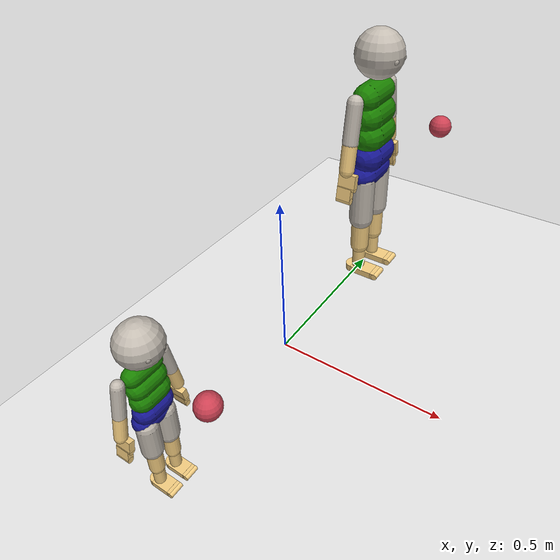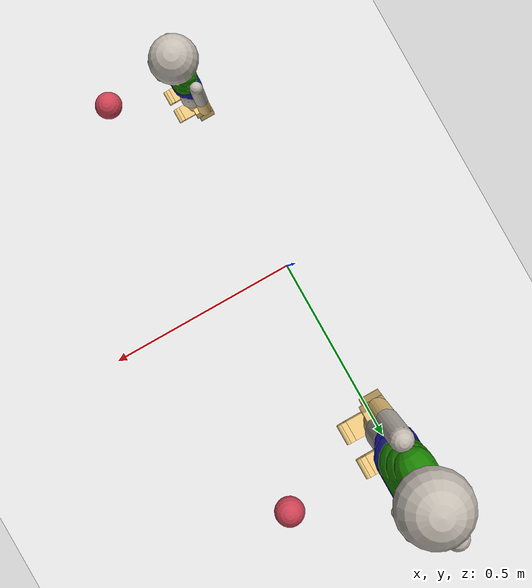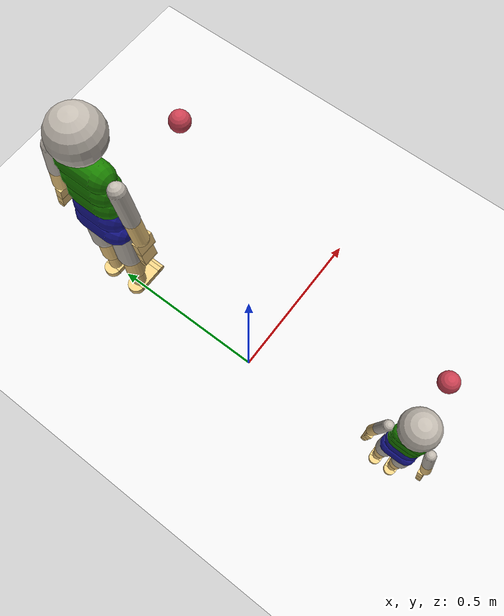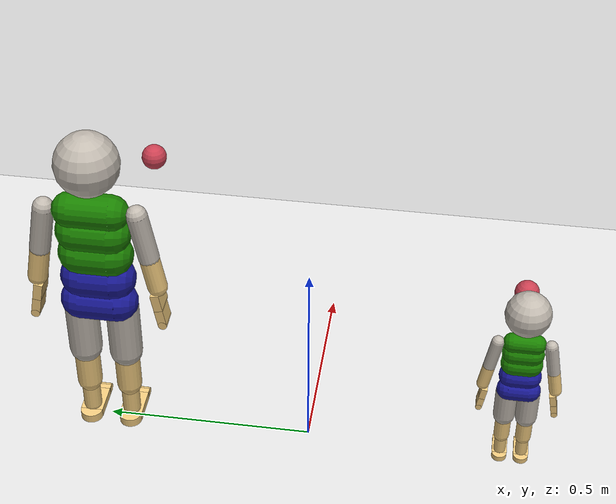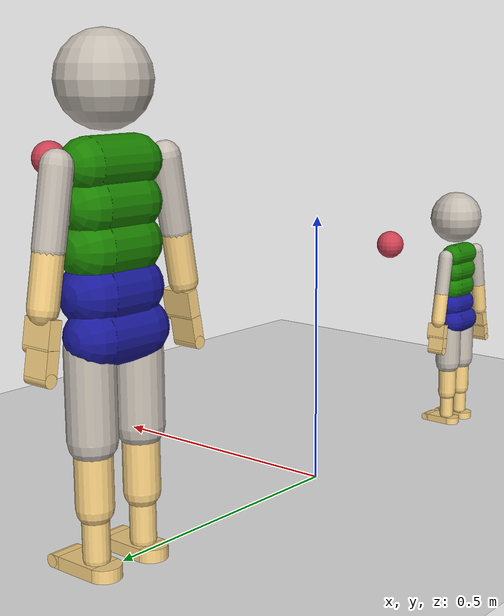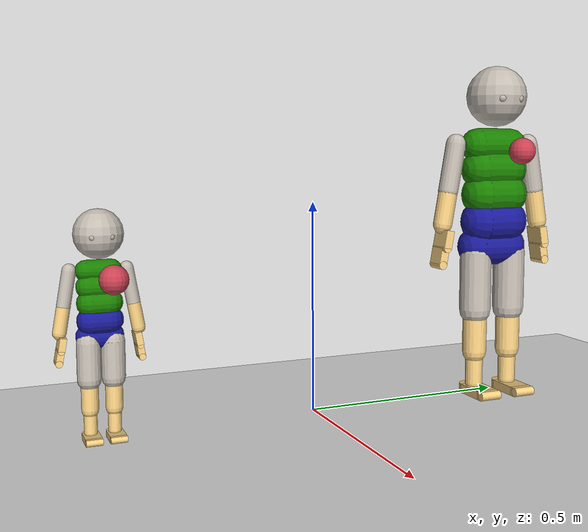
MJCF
<mujoco model="MIMo">

    <compiler inertiafromgeom="true" angle="degree" />
    <option timestep="0.005" iterations="50" tolerance="1e-10" solver="Newton" jacobian="dense" cone="elliptic" impratio="1.0" />
    <size nconmax="1000" njmax="5000" nstack="10000000" />

    <visual>
        <map force="0.1" fogend="10" shadowclip="3" />
        <headlight active="0" />
        <quality shadowsize="0" />
    </visual>

    <default>
		<default class="mimo">
        	<joint limited="true" damping=".1" stiffness=".1" armature="0.001" solimplimit="0.98 0.99 0.001 .5 1" solreflimit="0.02 1" />
        	<geom condim="3" material="skin" friction="1 0.005 0.0002" solimp="0.95 0.99 0.001 0.5 1" solref="0.005 1" />
        	<motor ctrlrange="-1 1" ctrllimited="true" forcelimited="true" />
		</default>
    </default>

    <asset>

        <!-- MIMo. -->
        <texture name="tex_head_default" type="cube" fileright="tex/head_front.png" fileleft="tex/head_back.png" fileup="tex/head_left.png" filedown="tex/head_right.png" filefront="tex/head_top.png" rgb1="0.95 .8 .5" />
		<texture name="tex_head_happy" type="cube" fileright="tex/head_front_happy.png" fileleft="tex/head_back.png" fileup="tex/head_left.png" filedown="tex/head_right.png" filefront="tex/head_top.png" rgb1="0.95 .8 .5" />
		<texture name="tex_head_sad" type="cube" fileright="tex/head_front_sad.png" fileleft="tex/head_back.png" fileup="tex/head_left.png" filedown="tex/head_right.png" filefront="tex/head_top.png" rgb1="0.95 .8 .5" />
		<texture name="tex_head_surprised" type="cube" fileright="tex/head_front_surprised.png" fileleft="tex/head_back.png" fileup="tex/head_left.png" filedown="tex/head_right.png" filefront="tex/head_top.png" rgb1="0.95 .8 .5" />
		<texture name="tex_head_angry" type="cube" fileright="tex/head_front_angry.png" fileleft="tex/head_back.png" fileup="tex/head_left.png" filedown="tex/head_right.png" filefront="tex/head_top.png" rgb1="0.95 .8 .5" />
		<texture name="tex_head_disgusted" type="cube" fileright="tex/head_front_disgusted.png" fileleft="tex/head_back.png" fileup="tex/head_left.png" filedown="tex/head_right.png" filefront="tex/head_top.png" rgb1="0.95 .8 .5" />
		<texture name="tex_head_scared" type="cube" fileright="tex/head_front_scared.png" fileleft="tex/head_back.png" fileup="tex/head_left.png" filedown="tex/head_right.png" filefront="tex/head_top.png" rgb1="0.95 .8 .5" />
		<texture name="tex_top_sleeve" type="cube" fileright="tex/sleeve_right.png" fileleft="tex/sleeve_left.png" fileup="tex/sleeve_up.png" filedown="tex/sleeve_down.png" filefront="tex/sleeve_front.png" fileback="tex/sleeve_back.png" rgb1="0.95 .8 .5" />
		<texture name="tex_pants_leg" type="cube" fileright="tex/leg_right.png" fileleft="tex/leg_left.png" fileup="tex/leg_up.png" filedown="tex/leg_down.png" filefront="tex/leg_front.png" fileback="tex/leg_back.png" rgb1="0.95 .8 .5" />
		<texture name="tex_eye_left" type="cube" fileright="tex/eye_pupil_left.png" rgb1="1 1 1" />
		<texture name="tex_eye_right" type="cube" fileright="tex/eye_pupil_right.png" rgb1="1 1 1" />
		<material name="skin" rgba="0.95 0.8 0.5 1" specular=".15" shininess=".7" />
		<material name="buttons" rgba=".05 .05 .05 1" specular=".9" shininess=".9" />
		<material name="head" texture="tex_head_default" texuniform="true" specular=".0" shininess=".0" />
		<material name="head_happy" texture="tex_head_happy" texuniform="true" specular=".0" shininess=".0" />
		<material name="head_sad" texture="tex_head_sad" texuniform="true" specular=".0" shininess=".0" />
		<material name="head_surprised" texture="tex_head_surprised" texuniform="true" specular=".0" shininess=".0" />
		<material name="head_angry" texture="tex_head_angry" texuniform="true" specular=".0" shininess=".0" />
		<material name="head_scared" texture="tex_head_scared" texuniform="true" specular=".0" shininess=".0" />
		<material name="top_up" rgba=".1 .5 0.0 1" specular=".0" shininess=".0" />
		<material name="top_middle" rgba=".1 .5 0.0 1" specular=".0" shininess=".0" />
		<material name="top_down" rgba=".1 .5 0.0 1" specular=".0" shininess=".0" />
		<material name="top_sleeve" texture="tex_top_sleeve" texuniform="true" specular=".0" shininess=".0" />
		<material name="pants_up" rgba="0.1 0.1 0.6 1" specular=".0" shininess=".0" />
		<material name="pants_down" rgba="0.1 0.1 0.6 1" specular=".0" shininess=".0" />
		<material name="pants_leg" texture="tex_pants_leg" texuniform="true" specular=".0" shininess=".0" />
		<material name="eye_left" texture="tex_eye_left" texuniform="true" specular=".0" shininess=".0" />
		<material name="eye_right" texture="tex_eye_right" texuniform="true" specular=".0" shininess=".0" />

        <!-- Floor. -->
		<texture name="texfloor" builtin="checker" height="100" width="100" rgb1="0.9 0.9 0.9" rgb2="0.9 0.9 0.9" type="2d" mark="edge" markrgb="0.7 0.7 0.7"/>
        <material name="matfloor" reflectance="0" shininess="0" specular="0" texrepeat="25 25" texture="texfloor"/>

        <!-- Colors. -->
        <material name="red" rgba=".79 .25 .32 1" shininess="0.99" reflectance="0"/>

        <!-- Misc. -->
		<texture type="skybox" builtin="gradient" rgb1=".8 .8 .8" rgb2=".9 .9 .9" width="100" height="100"/>
		<material name="mattransparent" reflectance="0" shininess="0" specular="0" rgba="1 1 1 0"/>

    </asset>

    <include file="mimo_ages/MIMo_meta_0.xml" />
    <include file="mimo_ages/MIMo_meta_24.xml" />

    <worldbody>

        <light pos="0 0 5" dir="0 0 -1" directional="true" ambient="0.2 0.2 0.2" diffuse="0.1 0.1 0.1" specular="0 0 0" />
        <light pos="2 2 2" dir="-1 -1 -1" directional="true" ambient="0.05 0.05 0.05" diffuse="0.2 0.2 0.2" specular="0.3 0.3 0.3" castshadow="false" />
        <light pos="2 -2 2" dir="-1 1 -1" directional="true" ambient="0.05 0.05 0.05" diffuse="0.2 0.2 0.2" specular="0.3 0.3 0.3" castshadow="false" />
        <light pos="-2 2 2" dir="1 -1 -1" directional="true" ambient="0.05 0.05 0.05" diffuse="0.2 0.2 0.2" specular="0.3 0.3 0.3" castshadow="false" />
        <light pos="-2 -2 2" dir="1 1 -1" directional="true" ambient="0.05 0.05 0.05" diffuse="0.2 0.2 0.2" specular="0.3 0.3 0.3" castshadow="false" />

        <geom name="transparent" size="2 2 .0001" type="plane"  material="mattransparent" pos="0 0 0" conaffinity="1"/>
        <geom name="floor" size="2 2 .01" type="plane"  material="matfloor" pos="0 0 -0.01" conaffinity="1"/>

        <body name="mimo_location_0" pos="0 -0.5 0.22" euler="0 0 0">
			<freejoint/>
			<include file="mimo_ages/MIMo_model_0.xml" />
		</body>

        <geom name="ball1" type="sphere" size="0.03" pos="0.18 -0.5 0.37" material="red"/>
        <camera name="main1" pos="0.18 -0.5 0.57" euler="0 0 -90" fovy="60"/>

        <body name="mimo_location_24" pos="0 0.5 0.37" euler="0 0 0">
			<freejoint/>
			<include file="mimo_ages/MIMo_model_24.xml" />
		</body>

        <geom name="ball2" type="sphere" size="0.03" pos="0.25 0.41 0.62" material="red"/>
        <camera name="main2" pos="0.25 0.41 0.82" euler="0 0 -90" fovy="60"/>

	</worldbody>

</mujoco>

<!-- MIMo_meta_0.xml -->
<mujoco model="MIMo">

	<size nuser_actuator="3" />

	<contact>
		<pair geom1="lb_0" geom2="ub1_0" condim="1" />
		<exclude body1="left_eye_0" body2="upper_body_0" />
		<exclude body1="right_eye_0" body2="upper_body_0" />
	</contact>

	<tendon>
		<fixed class="mimo" name="hip_bend_0" limited="true" range="-.01 .01">
			<joint joint="robot:hip_bend1_0" coef="1" />
			<joint joint="robot:hip_bend2_0" coef="-1" />
		</fixed>
		<fixed class="mimo" name="hip_rotation_0" limited="true" range="-.01 .01">
			<joint joint="robot:hip_rot1_0" coef="1" />
			<joint joint="robot:hip_rot2_0" coef="-1" />
		</fixed>
		<fixed class="mimo" name="hip_lean_0" limited="true" range="-.01 .01">
			<joint joint="robot:hip_lean1_0" coef="1" />
			<joint joint="robot:hip_lean2_0" coef="-.5" />
		</fixed>
		<fixed class="mimo" name="head_limits1_0" limited="true" range="-2.1 2.1">
			<joint joint="robot:head_swivel_0" coef="1" />
			<joint joint="robot:head_tilt_side_0" coef="1" />
		</fixed>
		<fixed class="mimo" name="head_limits2_0" limited="true" range="-2.1 2.1">
			<joint joint="robot:head_tilt_0" coef="1" />
			<joint joint="robot:head_tilt_side_0" coef="1" />
		</fixed>
		<fixed class="mimo" name="head_limits3_0" limited="true" range="-2.1 2.1">
			<joint joint="robot:head_swivel_0" coef="1" />
			<joint joint="robot:head_tilt_0" coef="1" />
		</fixed>
		<fixed class="mimo" name="head_limits1_sym_0" limited="true" range="-2.1 2.1">
			<joint joint="robot:head_swivel_0" coef="1" />
			<joint joint="robot:head_tilt_side_0" coef="-1" />
		</fixed>
		<fixed class="mimo" name="head_limits2_sym_0" limited="true" range="-2.1 2.1">
			<joint joint="robot:head_tilt_0" coef="1" />
			<joint joint="robot:head_tilt_side_0" coef="-1" />
		</fixed>
		<fixed class="mimo" name="head_limits3_sym_0" limited="true" range="-2.1 2.1">
			<joint joint="robot:head_swivel_0" coef="1" />
			<joint joint="robot:head_tilt_0" coef="-1" />
		</fixed>
	</tendon>

	<sensor>
		<accelerometer name="vestibular_acc_0" site="vestibular_0" />
		<gyro name="vestibular_gyro_0" site="vestibular_0" />

		<torque name="proprio:neck_0" site="torque_neck_0" />
		<torque name="proprio:left_eye_0" site="torque_left_eye_0" />
		<torque name="proprio:right_eye_0" site="torque_right_eye_0" />

		<torque name="proprio:trunk_upper_0" site="torque_ub_0" />
		<torque name="proprio:trunk_lower_0" site="torque_lb_0" />

		<torque name="proprio:right_shoulder_0" site="torque_right_shoulder_0" />
		<torque name="proprio:right_elbow_0" site="torque_right_elbow_0" />
		<torque name="proprio:right_wrist_0" site="torque_right_wrist_0" />
		<torque name="proprio:right_fingers_0" site="torque_right_fingers_0" />

		<torque name="proprio:left_shoulder_0" site="torque_left_shoulder_0" />
		<torque name="proprio:left_elbow_0" site="torque_left_elbow_0" />
		<torque name="proprio:left_wrist_0" site="torque_left_wrist_0" />
		<torque name="proprio:left_fingers_0" site="torque_left_fingers_0" />

		<torque name="proprio:right_hip_0" site="torque_right_hip_0" />
		<torque name="proprio:right_knee_0" site="torque_right_knee_0" />
		<torque name="proprio:right_ankle_0" site="torque_right_ankle_0" />
		<torque name="proprio:right_toes_0" site="torque_right_toes_0" />

		<torque name="proprio:left_hip_0" site="torque_left_hip_0" />
		<torque name="proprio:left_knee_0" site="torque_left_knee_0" />
		<torque name="proprio:left_ankle_0" site="torque_left_ankle_0" />
		<torque name="proprio:left_toes_0" site="torque_left_toes_0" />
	</sensor>

    <actuator>
		<motor class="mimo" name="act:hip_bend_0" joint="robot:hip_bend1_0" gear="1.9656450510895171" forcerange="-1 .765" user=".8574 32.93 22.97" />
		<motor class="mimo" name="act:hip_twist_0" joint="robot:hip_rot1_0" gear="0.6744131886063277" forcerange="-1 1" user="1.699 8.136 8.136" />
		<motor class="mimo" name="act:hip_lean_0" joint="robot:hip_lean1_0" gear="1.346968489640737" forcerange="-1 1" user="1.278 1.264 1.264" />

		<motor class="mimo" name="act:head_swivel_0" joint="robot:head_swivel_0" gear="0.7170287341631916" forcerange="-1 1" user=".6665 24.87 24.87" />
		<motor class="mimo" name="act:head_tilt_0" joint="robot:head_tilt_0" gear="1.3145526792991844" forcerange="-1 .55" user=".9338 31.39 16.86" />
		<motor class="mimo" name="act:head_tilt_side_0" joint="robot:head_tilt_side_0" gear="0.7170287341631916" forcerange="-1 1" user="1.068 15.69 15.69" />

		<motor class="mimo" name="act:left_eye_horizontal_0" joint="robot:left_eye_horizontal_0" gear="0.002151086202489574" forcerange="-1 1" user="5.110 .03025 .03025" />
		<motor class="mimo" name="act:left_eye_vertical_0" joint="robot:left_eye_vertical_0" gear="0.002151086202489574" forcerange="-1 1" user="6.179 .02619 .02771" />
		<motor class="mimo" name="act:left_eye_torsional_0" joint="robot:left_eye_torsional_0" gear="0.0014738923980021155" forcerange="-1 1" user="25.03 .003686 .003686" />
		<motor class="mimo" name="act:right_eye_horizontal_0" joint="robot:right_eye_horizontal_0" gear="0.002151086202489574" forcerange="-1 1" user="5.110 .03025 .03025" />
		<motor class="mimo" name="act:right_eye_vertical_0" joint="robot:right_eye_vertical_0" gear="0.002151086202489574" forcerange="-1 1" user="6.179 .02619 .02771" />
		<motor class="mimo" name="act:right_eye_torsional_0" joint="robot:right_eye_torsional_0" gear="0.0014738923980021155" forcerange="-1 1" user="25.03 .003686 .003686" />

		<motor class="mimo" name="act:right_shoulder_horizontal_0" joint="robot:right_shoulder_horizontal_0" gear="0.4993398493928391" forcerange="-1 1" user="1.811 18.80 15.30" />
		<motor class="mimo" name="act:right_shoulder_abduction_0" joint="robot:right_shoulder_ad_ab_0" gear="1.1096441097618646" forcerange="-.6875 1" user=".8793 44.17 69.23" />
		<motor class="mimo" name="act:right_shoulder_internal_0" joint="robot:right_shoulder_rotation_0" gear="0.6935275686011654" forcerange="-1 .64" user="1.498 25.09 17.10" />
		<motor class="mimo" name="act:right_elbow_0" joint="robot:right_elbow_0" gear="1.1132438625653438" forcerange="-1 .83" user="1.566 35.43 27.04" />
		<motor class="mimo" name="act:right_wrist_rotation_0" joint="robot:right_hand1_0" gear="0.248617332016975" forcerange="-1 1" user="1.513 7.842 7.842" />
		<motor class="mimo" name="act:right_wrist_flexion_0" joint="robot:right_hand2_0" gear="0.44040784528721294" forcerange="-1 .57" user="1.455 13.66 7.874" />
		<motor class="mimo" name="act:right_wrist_ulnar_0" joint="robot:right_hand3_0" gear="0.3374092363087518" forcerange="-.87 1" user="2.254 5.155 6.021" />
		<motor class="mimo" name="act:right_fingers_0" joint="robot:right_fingers_0" gear="0.24506565584530396" forcerange="-1 .33" user="3.019 6.854 2.551" />

		<motor class="mimo" name="act:left_shoulder_horizontal_0" joint="robot:left_shoulder_horizontal_0" gear="0.4993398493928391" forcerange="-1 1" user="1.811 18.80 15.30" />
		<motor class="mimo" name="act:left_shoulder_abduction_0" joint="robot:left_shoulder_ad_ab_0" gear="1.1096441097618646" forcerange="-.6875 1" user=".8793 44.17 69.23" />
		<motor class="mimo" name="act:left_shoulder_internal_0" joint="robot:left_shoulder_rotation_0" gear="0.6935275686011654" forcerange="-1 .64" user="1.498 25.09 17.10" />
		<motor class="mimo" name="act:left_elbow_0" joint="robot:left_elbow_0" gear="1.1132438625653438" forcerange="-1 .83" user="1.566 35.43 27.04" />
		<motor class="mimo" name="act:left_wrist_rotation_0" joint="robot:left_hand1_0" gear="0.248617332016975" forcerange="-1 1" user="1.513 7.842 7.842" />
		<motor class="mimo" name="act:left_wrist_flexion_0" joint="robot:left_hand2_0" gear="0.44040784528721294" forcerange="-1 .57" user="1.455 13.66 7.874" />
		<motor class="mimo" name="act:left_wrist_ulnar_0" joint="robot:left_hand3_0" gear="0.3374092363087518" forcerange="-.87 1" user="2.254 5.155 6.021" />
		<motor class="mimo" name="act:left_fingers_0" joint="robot:left_fingers_0" gear="0.24506565584530396" forcerange="-1 .33" user="3.019 6.854 2.551" />

		<motor class="mimo" name="act:right_hip_flex_0" joint="robot:right_hip1_0" gear="2.6261705346445345" forcerange="-1 1" user="1.083 71.25 92.49" />
		<motor class="mimo" name="act:right_hip_abduction_0" joint="robot:right_hip2_0" gear="2.048413017022737" forcerange="-1 1" user="1.488 24.81 29.20" />
		<motor class="mimo" name="act:right_hip_rotation_0" joint="robot:right_hip3_0" gear="1.1620804615802063" forcerange="-.75 1" user="1.860 12.32 15.78" />
		<motor class="mimo" name="act:right_knee_0" joint="robot:right_knee_0" gear="2.8438505152820945" forcerange="-.65 1" user="1.450 63.16 89.27" />
		<motor class="mimo" name="act:right_foot_flexion_0" joint="robot:right_foot1_0" gear="1.2797273955413133" forcerange="-1 .5" user="1.430 21.34 11.87" />
		<motor class="mimo" name="act:right_foot_inversion_0" joint="robot:right_foot2_0" gear="0.3927205764095036" forcerange="-.91 1" user="1.988 4.184 4.645" />
		<motor class="mimo" name="act:right_foot_rotation_0" joint="robot:right_foot3_0" gear="0.40626266525121063" forcerange="-1 1" user="2.688 3.868 3.625" />
		<motor class="mimo" name="act:right_toes_0" joint="robot:right_toes_0" gear="0.11172223294408291" forcerange="-1 .3" user="1.290 2.947 .8440" />

		<motor class="mimo" name="act:left_hip_flex_0" joint="robot:left_hip1_0" gear="2.6261705346445345" forcerange="-1 1" user="1.083 71.25 92.49" />
		<motor class="mimo" name="act:left_hip_abduction_0" joint="robot:left_hip2_0" gear="2.048413017022737" forcerange="-1 1" user="1.488 24.81 29.20" />
		<motor class="mimo" name="act:left_hip_rotation_0" joint="robot:left_hip3_0" gear="1.1620804615802063" forcerange="-.75 1" user="1.860 12.32 15.78" />
		<motor class="mimo" name="act:left_knee_0" joint="robot:left_knee_0" gear="2.8438505152820945" forcerange="-.65 1" user="1.450 63.16 89.27" />
		<motor class="mimo" name="act:left_foot_flexion_0" joint="robot:left_foot1_0" gear="1.2797273955413133" forcerange="-1 .5" user="1.430 21.34 11.87" />
		<motor class="mimo" name="act:left_foot_inversion_0" joint="robot:left_foot2_0" gear="0.3927205764095036" forcerange="-.91 1" user="1.988 4.184 4.645" />
		<motor class="mimo" name="act:left_foot_rotation_0" joint="robot:left_foot3_0" gear="0.40626266525121063" forcerange="-1 1" user="2.688 3.868 3.625" />
		<motor class="mimo" name="act:left_toes_0" joint="robot:left_toes_0" gear="0.11172223294408291" forcerange="-1 .3" user="1.290 2.947 .8440" />
	</actuator>

	<equality>
		<joint name="robot:hip_lean1_0" joint1="robot:hip_lean1_0" active="false" polycoef="0 1 0 0 0" />
		<joint name="robot:hip_rot1_0" joint1="robot:hip_rot1_0" active="false" polycoef="0 1 0 0 0" />
		<joint name="robot:hip_bend1_0" joint1="robot:hip_bend1_0" active="false" polycoef="0 1 0 0 0" />
		<joint name="robot:hip_lean2_0" joint1="robot:hip_lean2_0" active="false" polycoef="0 1 0 0 0" />
		<joint name="robot:hip_rot2_0" joint1="robot:hip_rot2_0" active="false" polycoef="0 1 0 0 0" />
		<joint name="robot:hip_bend2_0" joint1="robot:hip_bend2_0" active="false" polycoef="0 1 0 0 0" />
		<joint name="robot:head_swivel_0" joint1="robot:head_swivel_0" active="false" polycoef="0 1 0 0 0" />
		<joint name="robot:head_tilt_0" joint1="robot:head_tilt_0" active="false" polycoef="0 1 0 0 0" />
		<joint name="robot:head_tilt_side_0" joint1="robot:head_tilt_side_0" active="false" polycoef="0 1 0 0 0" />
		<joint name="robot:left_eye_horizontal_0" joint1="robot:left_eye_horizontal_0" active="false" polycoef="0 1 0 0 0" />
		<joint name="robot:left_eye_vertical_0" joint1="robot:left_eye_vertical_0" active="false" polycoef="0 1 0 0 0" />
		<joint name="robot:left_eye_torsional_0" joint1="robot:left_eye_torsional_0" active="false" polycoef="0 1 0 0 0" />
		<joint name="robot:right_eye_horizontal_0" joint1="robot:right_eye_horizontal_0" active="false" polycoef="0 1 0 0 0" />
		<joint name="robot:right_eye_vertical_0" joint1="robot:right_eye_vertical_0" active="false" polycoef="0 1 0 0 0" />
		<joint name="robot:right_eye_torsional_0" joint1="robot:right_eye_torsional_0" active="false" polycoef="0 1 0 0 0" />
		<joint name="robot:right_shoulder_horizontal_0" joint1="robot:right_shoulder_horizontal_0" active="false" polycoef="0 1 0 0 0" />
		<joint name="robot:right_shoulder_ad_ab_0" joint1="robot:right_shoulder_ad_ab_0" active="false" polycoef="0 1 0 0 0" />
		<joint name="robot:right_shoulder_rotation_0" joint1="robot:right_shoulder_rotation_0" active="false" polycoef="0 1 0 0 0" />
		<joint name="robot:right_elbow_0" joint1="robot:right_elbow_0" active="false" polycoef="0 1 0 0 0" />
		<joint name="robot:right_hand1_0" joint1="robot:right_hand1_0" active="false" polycoef="0 1 0 0 0" />
		<joint name="robot:right_hand2_0" joint1="robot:right_hand2_0" active="false" polycoef="0 1 0 0 0" />
		<joint name="robot:right_hand3_0" joint1="robot:right_hand3_0" active="false" polycoef="0 1 0 0 0" />
		<joint name="robot:right_fingers_0" joint1="robot:right_fingers_0" active="false" polycoef="0 1 0 0 0" />
		<joint name="robot:left_shoulder_horizontal_0" joint1="robot:left_shoulder_horizontal_0" active="false" polycoef="0 1 0 0 0" />
		<joint name="robot:left_shoulder_ad_ab_0" joint1="robot:left_shoulder_ad_ab_0" active="false" polycoef="0 1 0 0 0" />
		<joint name="robot:left_shoulder_rotation_0" joint1="robot:left_shoulder_rotation_0" active="false" polycoef="0 1 0 0 0" />
		<joint name="robot:left_elbow_0" joint1="robot:left_elbow_0" active="false" polycoef="0 1 0 0 0" />
		<joint name="robot:left_hand1_0" joint1="robot:left_hand1_0" active="false" polycoef="0 1 0 0 0" />
		<joint name="robot:left_hand2_0" joint1="robot:left_hand2_0" active="false" polycoef="0 1 0 0 0" />
		<joint name="robot:left_hand3_0" joint1="robot:left_hand3_0" active="false" polycoef="0 1 0 0 0" />
		<joint name="robot:left_fingers_0" joint1="robot:left_fingers_0" active="false" polycoef="0 1 0 0 0" />
		<joint name="robot:right_hip1_0" joint1="robot:right_hip1_0" active="false" polycoef="0 1 0 0 0" />
		<joint name="robot:right_hip2_0" joint1="robot:right_hip2_0" active="false" polycoef="0 1 0 0 0" />
		<joint name="robot:right_hip3_0" joint1="robot:right_hip3_0" active="false" polycoef="0 1 0 0 0" />
		<joint name="robot:right_knee_0" joint1="robot:right_knee_0" active="false" polycoef="0 1 0 0 0" />
		<joint name="robot:right_foot1_0" joint1="robot:right_foot1_0" active="false" polycoef="0 1 0 0 0" />
		<joint name="robot:right_foot2_0" joint1="robot:right_foot2_0" active="false" polycoef="0 1 0 0 0" />
		<joint name="robot:right_foot3_0" joint1="robot:right_foot3_0" active="false" polycoef="0 1 0 0 0" />
		<joint name="robot:right_toes_0" joint1="robot:right_toes_0" active="false" polycoef="0 1 0 0 0" />
		<joint name="robot:left_hip1_0" joint1="robot:left_hip1_0" active="false" polycoef="0 1 0 0 0" />
		<joint name="robot:left_hip2_0" joint1="robot:left_hip2_0" active="false" polycoef="0 1 0 0 0" />
		<joint name="robot:left_hip3_0" joint1="robot:left_hip3_0" active="false" polycoef="0 1 0 0 0" />
		<joint name="robot:left_knee_0" joint1="robot:left_knee_0" active="false" polycoef="0 1 0 0 0" />
		<joint name="robot:left_foot1_0" joint1="robot:left_foot1_0" active="false" polycoef="0 1 0 0 0" />
		<joint name="robot:left_foot2_0" joint1="robot:left_foot2_0" active="false" polycoef="0 1 0 0 0" />
		<joint name="robot:left_foot3_0" joint1="robot:left_foot3_0" active="false" polycoef="0 1 0 0 0" />
		<joint name="robot:left_toes_0" joint1="robot:left_toes_0" active="false" polycoef="0 1 0 0 0" />
	</equality>

</mujoco>

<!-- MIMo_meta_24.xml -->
<mujoco model="MIMo">

	<size nuser_actuator="3" />

	<contact>
		<pair geom1="lb_24" geom2="ub1_24" condim="1" />
		<exclude body1="left_eye_24" body2="upper_body_24" />
		<exclude body1="right_eye_24" body2="upper_body_24" />
	</contact>

	<tendon>
		<fixed class="mimo" name="hip_bend_24" limited="true" range="-.01 .01">
			<joint joint="robot:hip_bend1_24" coef="1" />
			<joint joint="robot:hip_bend2_24" coef="-1" />
		</fixed>
		<fixed class="mimo" name="hip_rotation_24" limited="true" range="-.01 .01">
			<joint joint="robot:hip_rot1_24" coef="1" />
			<joint joint="robot:hip_rot2_24" coef="-1" />
		</fixed>
		<fixed class="mimo" name="hip_lean_24" limited="true" range="-.01 .01">
			<joint joint="robot:hip_lean1_24" coef="1" />
			<joint joint="robot:hip_lean2_24" coef="-.5" />
		</fixed>
		<fixed class="mimo" name="head_limits1_24" limited="true" range="-2.1 2.1">
			<joint joint="robot:head_swivel_24" coef="1" />
			<joint joint="robot:head_tilt_side_24" coef="1" />
		</fixed>
		<fixed class="mimo" name="head_limits2_24" limited="true" range="-2.1 2.1">
			<joint joint="robot:head_tilt_24" coef="1" />
			<joint joint="robot:head_tilt_side_24" coef="1" />
		</fixed>
		<fixed class="mimo" name="head_limits3_24" limited="true" range="-2.1 2.1">
			<joint joint="robot:head_swivel_24" coef="1" />
			<joint joint="robot:head_tilt_24" coef="1" />
		</fixed>
		<fixed class="mimo" name="head_limits1_sym_24" limited="true" range="-2.1 2.1">
			<joint joint="robot:head_swivel_24" coef="1" />
			<joint joint="robot:head_tilt_side_24" coef="-1" />
		</fixed>
		<fixed class="mimo" name="head_limits2_sym_24" limited="true" range="-2.1 2.1">
			<joint joint="robot:head_tilt_24" coef="1" />
			<joint joint="robot:head_tilt_side_24" coef="-1" />
		</fixed>
		<fixed class="mimo" name="head_limits3_sym_24" limited="true" range="-2.1 2.1">
			<joint joint="robot:head_swivel_24" coef="1" />
			<joint joint="robot:head_tilt_24" coef="-1" />
		</fixed>
	</tendon>

	<sensor>
		<accelerometer name="vestibular_acc_24" site="vestibular_24" />
		<gyro name="vestibular_gyro_24" site="vestibular_24" />

		<torque name="proprio:neck_24" site="torque_neck_24" />
		<torque name="proprio:left_eye_24" site="torque_left_eye_24" />
		<torque name="proprio:right_eye_24" site="torque_right_eye_24" />

		<torque name="proprio:trunk_upper_24" site="torque_ub_24" />
		<torque name="proprio:trunk_lower_24" site="torque_lb_24" />

		<torque name="proprio:right_shoulder_24" site="torque_right_shoulder_24" />
		<torque name="proprio:right_elbow_24" site="torque_right_elbow_24" />
		<torque name="proprio:right_wrist_24" site="torque_right_wrist_24" />
		<torque name="proprio:right_fingers_24" site="torque_right_fingers_24" />

		<torque name="proprio:left_shoulder_24" site="torque_left_shoulder_24" />
		<torque name="proprio:left_elbow_24" site="torque_left_elbow_24" />
		<torque name="proprio:left_wrist_24" site="torque_left_wrist_24" />
		<torque name="proprio:left_fingers_24" site="torque_left_fingers_24" />

		<torque name="proprio:right_hip_24" site="torque_right_hip_24" />
		<torque name="proprio:right_knee_24" site="torque_right_knee_24" />
		<torque name="proprio:right_ankle_24" site="torque_right_ankle_24" />
		<torque name="proprio:right_toes_24" site="torque_right_toes_24" />

		<torque name="proprio:left_hip_24" site="torque_left_hip_24" />
		<torque name="proprio:left_knee_24" site="torque_left_knee_24" />
		<torque name="proprio:left_ankle_24" site="torque_left_ankle_24" />
		<torque name="proprio:left_toes_24" site="torque_left_toes_24" />
	</sensor>

    <actuator>
		<motor class="mimo" name="act:hip_bend_24" joint="robot:hip_bend1_24" gear="11.445274022776466" forcerange="-1 .765" user=".8574 32.93 22.97" />
		<motor class="mimo" name="act:hip_twist_24" joint="robot:hip_rot1_24" gear="3.9268756807824734" forcerange="-1 1" user="1.699 8.136 8.136" />
		<motor class="mimo" name="act:hip_lean_24" joint="robot:hip_lean1_24" gear="7.842933522223948" forcerange="-1 1" user="1.278 1.264 1.264" />

		<motor class="mimo" name="act:head_swivel_24" joint="robot:head_swivel_24" gear="1.9723820572800088" forcerange="-1 1" user=".6665 24.87 24.87" />
		<motor class="mimo" name="act:head_tilt_24" joint="robot:head_tilt_24" gear="3.6160337716800153" forcerange="-1 .55" user=".9338 31.39 16.86" />
		<motor class="mimo" name="act:head_tilt_side_24" joint="robot:head_tilt_side_24" gear="1.9723820572800088" forcerange="-1 1" user="1.068 15.69 15.69" />

		<motor class="mimo" name="act:left_eye_horizontal_24" joint="robot:left_eye_horizontal_24" gear="0.005917146171840027" forcerange="-1 1" user="5.110 .03025 .03025" />
		<motor class="mimo" name="act:left_eye_vertical_24" joint="robot:left_eye_vertical_24" gear="0.005917146171840027" forcerange="-1 1" user="6.179 .02619 .02771" />
		<motor class="mimo" name="act:left_eye_torsional_24" joint="robot:left_eye_torsional_24" gear="0.004054340895520018" forcerange="-1 1" user="25.03 .003686 .003686" />
		<motor class="mimo" name="act:right_eye_horizontal_24" joint="robot:right_eye_horizontal_24" gear="0.005917146171840027" forcerange="-1 1" user="5.110 .03025 .03025" />
		<motor class="mimo" name="act:right_eye_vertical_24" joint="robot:right_eye_vertical_24" gear="0.005917146171840027" forcerange="-1 1" user="6.179 .02619 .02771" />
		<motor class="mimo" name="act:right_eye_torsional_24" joint="robot:right_eye_torsional_24" gear="0.004054340895520018" forcerange="-1 1" user="25.03 .003686 .003686" />

		<motor class="mimo" name="act:right_shoulder_horizontal_24" joint="robot:right_shoulder_horizontal_24" gear="2.1532200911365003" forcerange="-1 1" user="1.811 18.80 15.30" />
		<motor class="mimo" name="act:right_shoulder_abduction_24" joint="robot:right_shoulder_ad_ab_24" gear="4.78493353585889" forcerange="-.6875 1" user=".8793 44.17 69.23" />
		<motor class="mimo" name="act:right_shoulder_internal_24" joint="robot:right_shoulder_rotation_24" gear="2.9905834599118064" forcerange="-1 .64" user="1.498 25.09 17.10" />
		<motor class="mimo" name="act:right_elbow_24" joint="robot:right_elbow_24" gear="4.3602089879735" forcerange="-1 .83" user="1.566 35.43 27.04" />
		<motor class="mimo" name="act:right_wrist_rotation_24" joint="robot:right_hand1_24" gear="0.8041257744098732" forcerange="-1 1" user="1.513 7.842 7.842" />
		<motor class="mimo" name="act:right_wrist_flexion_24" joint="robot:right_hand2_24" gear="1.4244513718117757" forcerange="-1 .57" user="1.455 13.66 7.874" />
		<motor class="mimo" name="act:right_wrist_ulnar_24" joint="robot:right_hand3_24" gear="1.091313550984828" forcerange="-.87 1" user="2.254 5.155 6.021" />
		<motor class="mimo" name="act:right_fingers_24" joint="robot:right_fingers_24" gear="0.7926382633468751" forcerange="-1 .33" user="3.019 6.854 2.551" />

		<motor class="mimo" name="act:left_shoulder_horizontal_24" joint="robot:left_shoulder_horizontal_24" gear="2.1532200911365003" forcerange="-1 1" user="1.811 18.80 15.30" />
		<motor class="mimo" name="act:left_shoulder_abduction_24" joint="robot:left_shoulder_ad_ab_24" gear="4.78493353585889" forcerange="-.6875 1" user=".8793 44.17 69.23" />
		<motor class="mimo" name="act:left_shoulder_internal_24" joint="robot:left_shoulder_rotation_24" gear="2.9905834599118064" forcerange="-1 .64" user="1.498 25.09 17.10" />
		<motor class="mimo" name="act:left_elbow_24" joint="robot:left_elbow_24" gear="4.3602089879735" forcerange="-1 .83" user="1.566 35.43 27.04" />
		<motor class="mimo" name="act:left_wrist_rotation_24" joint="robot:left_hand1_24" gear="0.8041257744098732" forcerange="-1 1" user="1.513 7.842 7.842" />
		<motor class="mimo" name="act:left_wrist_flexion_24" joint="robot:left_hand2_24" gear="1.4244513718117757" forcerange="-1 .57" user="1.455 13.66 7.874" />
		<motor class="mimo" name="act:left_wrist_ulnar_24" joint="robot:left_hand3_24" gear="1.091313550984828" forcerange="-.87 1" user="2.254 5.155 6.021" />
		<motor class="mimo" name="act:left_fingers_24" joint="robot:left_fingers_24" gear="0.7926382633468751" forcerange="-1 .33" user="3.019 6.854 2.551" />

		<motor class="mimo" name="act:right_hip_flex_24" joint="robot:right_hip1_24" gear="10.79160451329873" forcerange="-1 1" user="1.083 71.25 92.49" />
		<motor class="mimo" name="act:right_hip_abduction_24" joint="robot:right_hip2_24" gear="8.41745152037301" forcerange="-1 1" user="1.488 24.81 29.20" />
		<motor class="mimo" name="act:right_hip_rotation_24" joint="robot:right_hip3_24" gear="4.775284997134688" forcerange="-.75 1" user="1.860 12.32 15.78" />
		<motor class="mimo" name="act:right_knee_24" joint="robot:right_knee_24" gear="12.524757082073558" forcerange="-.65 1" user="1.450 63.16 89.27" />
		<motor class="mimo" name="act:right_foot_flexion_24" joint="robot:right_foot1_24" gear="5.14155614876697" forcerange="-1 .5" user="1.430 21.34 11.87" />
		<motor class="mimo" name="act:right_foot_inversion_24" joint="robot:right_foot2_24" gear="1.5778320456533557" forcerange="-.91 1" user="1.988 4.184 4.645" />
		<motor class="mimo" name="act:right_foot_rotation_24" joint="robot:right_foot3_24" gear="1.6322400472276095" forcerange="-1 1" user="2.688 3.868 3.625" />
		<motor class="mimo" name="act:right_toes_24" joint="robot:right_toes_24" gear="0.4488660129875926" forcerange="-1 .3" user="1.290 2.947 .8440" />

		<motor class="mimo" name="act:left_hip_flex_24" joint="robot:left_hip1_24" gear="10.79160451329873" forcerange="-1 1" user="1.083 71.25 92.49" />
		<motor class="mimo" name="act:left_hip_abduction_24" joint="robot:left_hip2_24" gear="8.41745152037301" forcerange="-1 1" user="1.488 24.81 29.20" />
		<motor class="mimo" name="act:left_hip_rotation_24" joint="robot:left_hip3_24" gear="4.775284997134688" forcerange="-.75 1" user="1.860 12.32 15.78" />
		<motor class="mimo" name="act:left_knee_24" joint="robot:left_knee_24" gear="12.524757082073558" forcerange="-.65 1" user="1.450 63.16 89.27" />
		<motor class="mimo" name="act:left_foot_flexion_24" joint="robot:left_foot1_24" gear="5.14155614876697" forcerange="-1 .5" user="1.430 21.34 11.87" />
		<motor class="mimo" name="act:left_foot_inversion_24" joint="robot:left_foot2_24" gear="1.5778320456533557" forcerange="-.91 1" user="1.988 4.184 4.645" />
		<motor class="mimo" name="act:left_foot_rotation_24" joint="robot:left_foot3_24" gear="1.6322400472276095" forcerange="-1 1" user="2.688 3.868 3.625" />
		<motor class="mimo" name="act:left_toes_24" joint="robot:left_toes_24" gear="0.4488660129875926" forcerange="-1 .3" user="1.290 2.947 .8440" />
	</actuator>

	<equality>
		<joint name="robot:hip_lean1_24" joint1="robot:hip_lean1_24" active="false" polycoef="0 1 0 0 0" />
		<joint name="robot:hip_rot1_24" joint1="robot:hip_rot1_24" active="false" polycoef="0 1 0 0 0" />
		<joint name="robot:hip_bend1_24" joint1="robot:hip_bend1_24" active="false" polycoef="0 1 0 0 0" />
		<joint name="robot:hip_lean2_24" joint1="robot:hip_lean2_24" active="false" polycoef="0 1 0 0 0" />
		<joint name="robot:hip_rot2_24" joint1="robot:hip_rot2_24" active="false" polycoef="0 1 0 0 0" />
		<joint name="robot:hip_bend2_24" joint1="robot:hip_bend2_24" active="false" polycoef="0 1 0 0 0" />
		<joint name="robot:head_swivel_24" joint1="robot:head_swivel_24" active="false" polycoef="0 1 0 0 0" />
		<joint name="robot:head_tilt_24" joint1="robot:head_tilt_24" active="false" polycoef="0 1 0 0 0" />
		<joint name="robot:head_tilt_side_24" joint1="robot:head_tilt_side_24" active="false" polycoef="0 1 0 0 0" />
		<joint name="robot:left_eye_horizontal_24" joint1="robot:left_eye_horizontal_24" active="false" polycoef="0 1 0 0 0" />
		<joint name="robot:left_eye_vertical_24" joint1="robot:left_eye_vertical_24" active="false" polycoef="0 1 0 0 0" />
		<joint name="robot:left_eye_torsional_24" joint1="robot:left_eye_torsional_24" active="false" polycoef="0 1 0 0 0" />
		<joint name="robot:right_eye_horizontal_24" joint1="robot:right_eye_horizontal_24" active="false" polycoef="0 1 0 0 0" />
		<joint name="robot:right_eye_vertical_24" joint1="robot:right_eye_vertical_24" active="false" polycoef="0 1 0 0 0" />
		<joint name="robot:right_eye_torsional_24" joint1="robot:right_eye_torsional_24" active="false" polycoef="0 1 0 0 0" />
		<joint name="robot:right_shoulder_horizontal_24" joint1="robot:right_shoulder_horizontal_24" active="false" polycoef="0 1 0 0 0" />
		<joint name="robot:right_shoulder_ad_ab_24" joint1="robot:right_shoulder_ad_ab_24" active="false" polycoef="0 1 0 0 0" />
		<joint name="robot:right_shoulder_rotation_24" joint1="robot:right_shoulder_rotation_24" active="false" polycoef="0 1 0 0 0" />
		<joint name="robot:right_elbow_24" joint1="robot:right_elbow_24" active="false" polycoef="0 1 0 0 0" />
		<joint name="robot:right_hand1_24" joint1="robot:right_hand1_24" active="false" polycoef="0 1 0 0 0" />
		<joint name="robot:right_hand2_24" joint1="robot:right_hand2_24" active="false" polycoef="0 1 0 0 0" />
		<joint name="robot:right_hand3_24" joint1="robot:right_hand3_24" active="false" polycoef="0 1 0 0 0" />
		<joint name="robot:right_fingers_24" joint1="robot:right_fingers_24" active="false" polycoef="0 1 0 0 0" />
		<joint name="robot:left_shoulder_horizontal_24" joint1="robot:left_shoulder_horizontal_24" active="false" polycoef="0 1 0 0 0" />
		<joint name="robot:left_shoulder_ad_ab_24" joint1="robot:left_shoulder_ad_ab_24" active="false" polycoef="0 1 0 0 0" />
		<joint name="robot:left_shoulder_rotation_24" joint1="robot:left_shoulder_rotation_24" active="false" polycoef="0 1 0 0 0" />
		<joint name="robot:left_elbow_24" joint1="robot:left_elbow_24" active="false" polycoef="0 1 0 0 0" />
		<joint name="robot:left_hand1_24" joint1="robot:left_hand1_24" active="false" polycoef="0 1 0 0 0" />
		<joint name="robot:left_hand2_24" joint1="robot:left_hand2_24" active="false" polycoef="0 1 0 0 0" />
		<joint name="robot:left_hand3_24" joint1="robot:left_hand3_24" active="false" polycoef="0 1 0 0 0" />
		<joint name="robot:left_fingers_24" joint1="robot:left_fingers_24" active="false" polycoef="0 1 0 0 0" />
		<joint name="robot:right_hip1_24" joint1="robot:right_hip1_24" active="false" polycoef="0 1 0 0 0" />
		<joint name="robot:right_hip2_24" joint1="robot:right_hip2_24" active="false" polycoef="0 1 0 0 0" />
		<joint name="robot:right_hip3_24" joint1="robot:right_hip3_24" active="false" polycoef="0 1 0 0 0" />
		<joint name="robot:right_knee_24" joint1="robot:right_knee_24" active="false" polycoef="0 1 0 0 0" />
		<joint name="robot:right_foot1_24" joint1="robot:right_foot1_24" active="false" polycoef="0 1 0 0 0" />
		<joint name="robot:right_foot2_24" joint1="robot:right_foot2_24" active="false" polycoef="0 1 0 0 0" />
		<joint name="robot:right_foot3_24" joint1="robot:right_foot3_24" active="false" polycoef="0 1 0 0 0" />
		<joint name="robot:right_toes_24" joint1="robot:right_toes_24" active="false" polycoef="0 1 0 0 0" />
		<joint name="robot:left_hip1_24" joint1="robot:left_hip1_24" active="false" polycoef="0 1 0 0 0" />
		<joint name="robot:left_hip2_24" joint1="robot:left_hip2_24" active="false" polycoef="0 1 0 0 0" />
		<joint name="robot:left_hip3_24" joint1="robot:left_hip3_24" active="false" polycoef="0 1 0 0 0" />
		<joint name="robot:left_knee_24" joint1="robot:left_knee_24" active="false" polycoef="0 1 0 0 0" />
		<joint name="robot:left_foot1_24" joint1="robot:left_foot1_24" active="false" polycoef="0 1 0 0 0" />
		<joint name="robot:left_foot2_24" joint1="robot:left_foot2_24" active="false" polycoef="0 1 0 0 0" />
		<joint name="robot:left_foot3_24" joint1="robot:left_foot3_24" active="false" polycoef="0 1 0 0 0" />
		<joint name="robot:left_toes_24" joint1="robot:left_toes_24" active="false" polycoef="0 1 0 0 0" />
	</equality>

</mujoco>

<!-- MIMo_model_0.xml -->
<mujoco model="MIMo">

	<body childclass="mimo" name="hip_0" pos="0 0 0">

		<geom name="lb_0" type="capsule" size="0.027389307207886213 0.024536254373731397 0.0" mass="0.21521769633101118" material="pants_down" pos="-0.002 0 0.002853052834154814" euler="90 0 0" />
		<site name="lowerBody_center_0" type="sphere" size=".01 .01 .01" pos="0 0 0" />
		<body name="lower_body_0" pos="0.002 0 0.04336640307915316">
			<joint name="robot:hip_lean1_0" type="hinge" pos="0 0 -.05" axis="1 0 0" range="-14 14" stiffness="3.38" damping="0.77" frictionloss=".049" armature="0.01" />
			<joint name="robot:hip_rot1_0" type="hinge" pos="0 0 -.05" axis="0 0 1" range="-18 18" stiffness="1.45" damping="0.29" frictionloss=".018" armature="0.01" />
			<joint name="robot:hip_bend1_0" type="hinge" pos="0 0 -0.05" axis="0 1 0" range="-17 30.5" stiffness="2.20" damping="0.84" frictionloss="0.040" armature="0.01" />
			<site name="torque_lb_0" type="sphere" size="0.01" pos="0 0 0" group="4" />
			<geom name="cb_0" type="capsule" size="0.030242360042041023 0.01997136983908369 0.0" mass="0.24607720890057327" material="pants_up" contype="0" pos="0.005 0 -0.004564884534647701" euler="90 0 0" />

			<body name="upper_body_0" pos="-0.002 0 0.05192556158161761">
				<joint name="robot:hip_lean2_0" type="hinge" pos="0 0 -.05" axis="1 0 0" range="-27 27" stiffness="1.69" damping="0.38" frictionloss=".024" armature="0.01" />
				<joint name="robot:hip_rot2_0" type="hinge" pos="0 0 -.05" axis="0 0 1" range="-18 18" stiffness="1.45" damping="0.29" frictionloss=".018" armature="0.01" />
				<joint name="robot:hip_bend2_0" type="hinge" pos="0 0 -.05" axis="0 1 0" range="-17 30.5" stiffness="2.20" damping="0.84" frictionloss="0.040" armature="0.01" />
				<site name="torque_ub_0" type="sphere" size="0.01" pos="0 0 0" group="4" />
				<geom name="ub1_0" type="capsule" size="0.029671749475210063 0.019971369839083694 0.0" mass="0.20217532557614493" material="top_down" pos="0.007 0 -0.018259538138590808" euler="90 0 0" />
				<geom name="ub2_0" type="capsule" size="0.027389307207886217 0.02225381210640754 0.0" mass="0.1764807404565155" material="top_middle" pos="0.004 0 0.017118317004928885" euler="90 0 0" />
				<geom name="ub3_0" type="capsule" size="0.02339503324006947 0.026818696641055243 0.0" mass="0.13408374606534068" material="top_up" pos="0 0 0.05135495101478663" euler="90 0 0" />

				<body name="head_0" pos="0 0 0.07703242652217995">
					<geom name="head_0" type="sphere" size="0.05408066509626227 0.0 0.0" mass="0.7069903318849068" material="head_angry" pos="0.01 0 0.05408066509626227" />
					<site name="vestibular_0" type="sphere" size="0.01" pos="0.01 0 0.0735" group="4" />
					<site name="torque_neck_0" type="sphere" size="0.01" pos="0 0 0" group="4" />
					<joint name="robot:head_swivel_0" type="hinge" pos="0 0 0" axis="0 0 1" range="-111 111" stiffness=".23" damping=".29" frictionloss=".018" armature="0.005" />
					<joint name="robot:head_tilt_0" type="hinge" pos="0 0 0.0123" axis="0 1 0" range="-70 81" stiffness=".45" damping=".53" frictionloss=".018" armature="0.005" />
					<joint name="robot:head_tilt_side_0" type="hinge" pos="0 0 0.0245" axis="1 0 0" range="-70 70" stiffness=".37" damping=".29" frictionloss=".018" armature="0.005" />
					<body name="left_eye_0" pos="0.0525053953297736 0.01902688836542076 0.050573943004907085">
						<site name="torque_left_eye_0" type="sphere" size="0.01" pos="0 0 0" group="4" />
						<joint name="robot:left_eye_horizontal_0" type="hinge" pos="0 0 0" axis="0 0 1" range="-45 45" stiffness=".00065" damping=".00042" frictionloss=".000054" armature=".0002" />
						<joint name="robot:left_eye_vertical_0" type="hinge" pos="0 0 0" axis="0 -1 0" range="-47 33" stiffness=".00065" damping=".00042" frictionloss=".000054" armature=".0002" />
						<joint name="robot:left_eye_torsional_0" type="hinge" pos="0 0 0" axis="-1 0 0" range="-8 8" stiffness=".00267" damping=".00042" frictionloss=".000037" armature=".0002" />
						<geom name="geom:left_eye1_0" type="sphere" material="eye_left" size="0.00827765282085647 0.0 0.0" mass="0.002499641837152237" pos="0 0 0" />
						<camera name="eye_left_0" mode="fixed" fovy="60" pos="0.01125 0 0" euler="90 -90 0" />
					</body>
					<body name="right_eye_0" pos="0.0525053953297736 -0.01902688836542076 0.050573943004907085">
						<site name="torque_right_eye_0" type="sphere" size="0.01" pos="0 0 0" group="4" />
						<joint name="robot:right_eye_horizontal_0" type="hinge" pos="0 0 0" axis="0 0 -1" range="-45 45" stiffness=".00065" damping=".00042" frictionloss=".000054" armature=".0002" />
						<joint name="robot:right_eye_vertical_0" type="hinge" pos="0 0 0" axis="0 -1 0" range="-47 33" stiffness=".00065" damping=".00042" frictionloss=".000054" armature=".0002" />
						<joint name="robot:right_eye_torsional_0" type="hinge" pos="0 0 0" axis="1 0 0" range="-8 8" stiffness=".00267" damping=".00042" frictionloss=".000037" armature=".0002" />
						<geom name="geom:right_eye1_0" type="sphere" material="eye_right" size="0.00827765282085647 0.0 0.0" mass="0.002499641837152237" pos="0 0 0" />
						<camera name="eye_right_0" mode="fixed" fovy="60" pos="0.01125 0 0" euler="90 -90 0" />
					</body>
				</body>

				<body name="right_upper_arm_0" pos="-0.005 -0.06115546532519245 0.05306678271527952" euler="170 0 0">

					<joint name="robot:right_shoulder_horizontal_0" type="hinge" pos="0 -.024 0" axis="0 1 -4" range="-28 118" stiffness=".09" damping=".05" frictionloss=".0009" armature="0.004" />
					<joint name="robot:right_shoulder_ad_ab_0" type="hinge" pos="0 0 0" axis="-1 0 0" range="-84 183" stiffness=".11" damping=".10" frictionloss=".0014" armature="0.004" />
					<joint name="robot:right_shoulder_rotation_0" type="hinge" pos="0 0 0" axis="0 0 -1" range="-99 67" stiffness=".12" damping=".07" frictionloss=".0008" armature="0.004" />
					<site name="torque_right_shoulder_0" type="sphere" size="0.01" pos="0 0 0" group="4" />
					<geom name="right_uarm1_0" type="capsule" material="top_sleeve" size="0.015018766465747228 0.03929202947840549 0.0" mass="0.07445711976502113" pos="0 0 0.03929202947840549" euler="0 0 0" />
					<body name="right_lower_arm_0" pos="0 0 0.0782562426539648" euler="0 0 0">
						<joint name="robot:right_elbow_0" type="hinge" pos="0 0 0" axis="0 -1 0" springref="-20" range="-146 5" stiffness=".13" damping=".11" frictionloss=".030" armature="0.002" />
						<site name="torque_right_elbow_0" type="sphere" size="0.01" pos="0 0 0" group="4" />
						<geom name="right_larm_0" type="capsule" size="0.01491020966829249 0.02856816294956921 0.0" mass="0.057301135481488394" pos="0 0 0.02856816294956921" />
						<body name="right_hand_0" pos="0.0 -0.007 0.06461905767388132" euler="0 0 0">
							<joint name="robot:right_hand1_0" type="hinge" pos="0 .007 0" axis="0 0 -1" springref="-20" range="-90 90" stiffness=".22" damping=".03" frictionloss=".007" armature="0.001" />
							<joint name="robot:right_hand2_0" type="hinge" pos="0 0 0" axis="-1 0 0" range="-92 86" stiffness=".33" damping=".11" frictionloss=".007" armature="0.001" />
							<joint name="robot:right_hand3_0" type="hinge" pos="0 0 0" axis="0 1 0" range="-53 48" stiffness=".38" damping=".11" frictionloss=".007" armature="0.001" />
							<site name="torque_right_wrist_0" type="sphere" size="0.01" pos="0 0 0" group="4" />
							<geom name="geom:right_hand1_0" type="box" size="0.020018572295820818 0.007313112788909835 0.014179719640670899" mass="0.015325482680760675" pos="0.0036565563944549176 0 0.014179719640670899" />
							<geom name="geom:right_hand2_0" type="cylinder" size="0.007513112788909835 0.019718572295820816 0.0" mass="0.006164993977145343" pos="0.0036565563944549176 0 0.028359439281341797" euler="0 90 0" />
							<body name="right_fingers_0" pos="0 0 0.028359439281341797">
								<joint name="robot:right_fingers_0" type="hinge" pos="0 0 0" axis="-1 0 0" springref="-40" range="-160 8" stiffness=".017" damping=".018" frictionloss=".0023" armature="0.0001" />
								<site name="torque_right_fingers_0" type="sphere" size="0.01" pos="0 0 0" group="4" />
								<geom name="geom:right_fingers1_0" type="box" size="0.01773073588141519 0.007313112788909835 0.014111547911629208" mass="0.013546322006289696" pos="0 0 0.014111547911629208" friction="5 0.02 0.01" />
								<geom name="geom:right_fingers2_0" type="cylinder" size="0.007513112788909835 0.017930735881415187 0.0" mass="0.00559589549592821" pos="0 0 0.028223095823258416" euler="0 90 0" friction="5 0.02 0.01" />
							</body>
						</body>
					</body>
				</body>

				<body name="left_upper_arm_0" pos="-0.005 0.06115546532519245 0.05306678271527952" euler="-170 0 0">

					<joint name="robot:left_shoulder_horizontal_0" type="hinge" pos="0 .024 0" axis="0 1 4" range="-28 118" stiffness=".09" damping=".05" frictionloss=".0009" armature="0.004" />
					<joint name="robot:left_shoulder_ad_ab_0" type="hinge" pos="0 0 0" axis="1 0 0" range="-84 183" stiffness=".11" damping=".10" frictionloss=".0014" armature="0.004" />
					<joint name="robot:left_shoulder_rotation_0" type="hinge" pos="0 0 0" axis="0 0 1" range="-99 67" stiffness=".12" damping=".07" frictionloss=".0008" armature="0.004" />
					<site name="torque_left_shoulder_0" type="sphere" size="0.01" pos="0 0 0" group="4" />
					<geom name="left_uarm1_0" type="capsule" material="top_sleeve" size="0.015018766465747228 0.03929202947840549 0.0" mass="0.07445711976502113" pos="0 0 0.03929202947840549" euler="0 0 0" />
					<body name="left_lower_arm_0" pos="0 0 0.0782562426539648" euler="0 0 0">
						<joint name="robot:left_elbow_0" type="hinge" pos="0 0 0" axis="0 -1 0" springref="-20" range="-146 5" stiffness=".13" damping=".11" frictionloss=".030" armature="0.002" />
						<site name="torque_left_elbow_0" type="sphere" size="0.01" pos="0 0 0" group="4" />
						<geom name="left_larm_0" type="capsule" size="0.01491020966829249 0.02856816294956921 0.0" mass="0.057301135481488394" pos="0 0 0.02856816294956921" />
						<body name="left_hand_0" pos="0 0.007 0.06461905767388132" euler="0 0 0">
							<joint name="robot:left_hand1_0" type="hinge" pos="0 -.007 0" axis="0 0 1" springref="-20" range="-90 90" stiffness=".22" damping=".03" frictionloss=".007" armature="0.001" />
							<joint name="robot:left_hand2_0" type="hinge" pos="0 0 0" axis="1 0 0" range="-92 86" stiffness=".33" damping=".11" frictionloss=".007" armature="0.001" />
							<joint name="robot:left_hand3_0" type="hinge" pos="0 0 0" axis="0 1 0" range="-53 48" stiffness=".38" damping=".11" frictionloss=".007" armature="0.001" />
							<site name="torque_left_wrist_0" type="sphere" size="0.01" pos="0 0 0" group="4" />
							<geom name="geom:left_hand1_0" type="box" size="0.020018572295820818 0.007313112788909835 0.014179719640670899" mass="0.015325482680760675" pos="0.0036565563944549176 0 0.014179719640670899" />
							<geom name="geom:left_hand2_0" type="cylinder" size="0.007513112788909835 0.019718572295820816 0.0" mass="0.006164993977145343" pos="0.0036565563944549176 0 0.028359439281341797" euler="0 90 0" />
							<body name="left_fingers_0" pos="0 0 0.028359439281341797">
								<joint name="robot:left_fingers_0" type="hinge" pos="0 0 0" axis="1 0 0" springref="-40" range="-160 8" stiffness=".017" damping=".018" frictionloss=".0023" armature="0.0001" />
								<site name="torque_left_fingers_0" type="sphere" size="0.01" pos="0 0 0" group="4" />
								<geom name="geom:left_fingers1_0" type="box" size="0.01773073588141519 0.007313112788909835 0.014111547911629208" mass="0.013546322006289696" pos="0 0 0.014111547911629208" friction="5 0.02 0.01" />
								<geom name="geom:left_fingers2_0" type="cylinder" size="0.007513112788909835 0.017930735881415187 0.0" mass="0.00559589549592821" pos="0 0 0.028223095823258416" euler="0 90 0" friction="5 0.02 0.01" />
							</body>
						</body>
					</body>
				</body>
			</body>
		</body>

		<body name="right_upper_leg_0" pos="0.005 -0.026090365627520186 -0.007">

			<joint name="robot:right_hip1_0" type="hinge" pos="0 0 0" axis="0 1 0" springref="-10" range="-133 20" stiffness="1.72" damping="1.27" frictionloss=".08" armature=".005" />
			<joint name="robot:right_hip2_0" type="hinge" pos="0 0 0" axis="1 0 0" range="-51 17" stiffness="3.51" damping="1.99" frictionloss=".062" armature=".005" />
			<joint name="robot:right_hip3_0" type="hinge" pos="0 0 0" axis="0 0 -1" range="-32 41" stiffness="2.16" damping="0.75" frictionloss=".027" armature=".005" />
			<site name="torque_right_hip_0" type="sphere" size="0.01" pos="0 0 0" group="4" />
			<geom name="geom:right_upper_leg1_0" type="capsule" material="pants_leg" contype="2" conaffinity="3" size="0.026090365627520186 0.040153927118548885 0.0" mass="0.26255139920108733" pos="0 0 -0.04143885278634245" euler="0 0 0" />
			<body name="right_lower_leg_0" pos="0 0 -0.08889643503555561">
				<joint name="robot:right_knee_0" type="hinge" pos="0 0 0" axis="0 -1 0" springref="-30" range="-145 4" stiffness="1.63" damping="0.53" frictionloss=".065" armature=".003" />
				<site name="torque_right_knee_0" type="sphere" size="0.01" pos="0 0 0" group="4" />
				<geom name="geom:right_lower_leg1_0" type="capsule" size="0.018818769051811315 0.030225476694967803 0.0" mass="0.09501304571557478" pos="0 0 -0.030225476694967803" euler="0 0 0" />
				<geom name="geom:right_lower_leg2_0" type="capsule" size="0.014411749505706513 0.019234394260434055 0.0" mass="0.037517363732522784" pos="0 0 -0.09203657678039567" euler="0 0 0" />
				<body name="right_foot_0" pos="0 0 -0.12157518800640076">
					<joint name="robot:right_foot1_0" type="hinge" pos="0 0 .015" axis="0 -1 0" springref="-10" range="-63 32" stiffness="1.29" damping="0.6" frictionloss=".019" armature=".003" />
					<joint name="robot:right_foot2_0" type="hinge" pos="0 0 .015" axis="1 0 0" range="-33 31" stiffness="0.96" damping="0.37" frictionloss=".011" armature=".0025" />
					<joint name="robot:right_foot3_0" type="hinge" pos="0 0 .015" axis="0 0 1" range="-20 30" stiffness="1.15" damping="0.38" frictionloss=".012" armature=".002" />
					<site name="torque_right_ankle_0" type="sphere" size="0.01" pos="0 0 0" group="4" />
					<geom name="geom:right_foot1_0" type="cylinder" size="0.017826719384593483 0.0068696112661762185 0.0" mass="0.011448856353630533" pos="-0.010838677207912798 0 0" euler="0 0 0" />
					<geom name="geom:right_foot2_0" type="box" size="0.023709606392309245 0.017926719384593483 0.006969611266176219" mass="0.01980530493099652" pos="0.012870929184396447 0 0" euler="0 0 0" friction="2 0.02 0.01" />
					<geom name="geom:right_foot3_0" type="cylinder" size="0.0068696112661762185 0.017726719384593484 0.0" mass="0.004364051606442294" pos="0.036580535576705694 0 0" euler="90 0 0" friction="2 0.02 0.01" />
					<body name="right_toes_0" pos="0.036580535576705694 0 0">
						<joint name="robot:right_toes_0" type="hinge" pos="0 0 0" axis="0 -1 0" range="-60 80" frictionloss=".005" armature=".0005" stiffness=".106" damping=".04" />
						<site name="torque_right_toes_0" type="sphere" size="0.01" pos="0 0 0" group="4" />
						<geom name="geom:right_toes1_0" type="box" size="0.004741921278461849 0.017826719384593483 0.0068696112661762185" mass="0.0036479983289069" pos="0.004741921278461849 0 0" euler="0 0 0" friction="2 0.02 0.01" />
						<geom name="geom:right_toes2_0" type="cylinder" size="0.006969611266176219 0.017926719384593483 0.0" mass="0.004270398396398938" pos="0.009483842556923697 0 0" euler="90 0 0" friction="2 0.02 0.01" />
					</body>
				</body>
			</body>
		</body>

		<body name="left_upper_leg_0" pos="0.005 0.026090365627520186 -0.007">

			<joint name="robot:left_hip1_0" type="hinge" pos="0 0 0" axis="0 1 0" springref="-10" range="-133 20" stiffness="1.72" damping="1.27" frictionloss=".08" armature=".005" />
			<joint name="robot:left_hip2_0" type="hinge" pos="0 0 0" axis="-1 0 0" range="-51 17" stiffness="3.51" damping="1.99" frictionloss=".062" armature=".005" />
			<joint name="robot:left_hip3_0" type="hinge" pos="0 0 0" axis="0 0 1" range="-32 41" stiffness="2.16" damping="0.75" frictionloss=".027" armature=".005" />
			<site name="torque_left_hip_0" type="sphere" size="0.01" pos="0 0 0" group="4" />
			<geom name="geom:left_upper_leg1_0" type="capsule" material="pants_leg" contype="2" conaffinity="3" size="0.026090365627520186 0.040153927118548885 0.0" mass="0.26255139920108733" pos="0 0 -0.04143885278634245" euler="0 0 0" />
			<body name="left_lower_leg_0" pos="0 0 -0.08889643503555561">
				<joint name="robot:left_knee_0" type="hinge" pos="0 0 0" axis="0 -1 0" springref="-30" range="-145 4" stiffness="1.63" damping="0.53" frictionloss=".065" armature=".003" />
				<site name="torque_left_knee_0" type="sphere" size="0.01" pos="0 0 0" group="4" />
				<geom name="geom:left_lower_leg1_0" type="capsule" size="0.018818769051811315 0.030225476694967803 0.0" mass="0.09501304571557478" pos="0 0 -0.030225476694967803" euler="0 0 0" />
				<geom name="geom:left_lower_leg2_0" type="capsule" size="0.014411749505706513 0.019234394260434055 0.0" mass="0.037517363732522784" pos="0 0 -0.09203657678039567" euler="0 0 0" />
				<body name="left_foot_0" pos="0 0 -0.12157518800640076">
					<joint name="robot:left_foot1_0" type="hinge" pos="0 0 .015" axis="0 -1 0" springref="-10" range="-63 32" stiffness="1.29" damping="0.6" frictionloss=".019" armature=".003" />
					<joint name="robot:left_foot2_0" type="hinge" pos="0 0 .015" axis="-1 0 0" range="-33 31" stiffness="0.96" damping="0.37" frictionloss=".011" armature=".0025" />
					<joint name="robot:left_foot3_0" type="hinge" pos="0 0 .015" axis="0 0 -1" range="-20 30" stiffness="1.15" damping="0.38" frictionloss=".012" armature=".002" />
					<site name="torque_left_ankle_0" type="sphere" size="0.01" pos="0 0 0" group="4" />
					<geom name="geom:left_foot1_0" type="cylinder" size="0.017826719384593483 0.0068696112661762185 0.0" mass="0.011448856353630533" pos="-0.010838677207912798 0 0" euler="0 0 0" />
					<geom name="geom:left_foot2_0" type="box" size="0.023709606392309245 0.017926719384593483 0.006969611266176219" mass="0.01980530493099652" pos="0.012870929184396447 0 0" euler="0 0 0" friction="2 0.02 0.01" />
					<geom name="geom:left_foot3_0" type="cylinder" size="0.0068696112661762185 0.017726719384593484 0.0" mass="0.004364051606442294" pos="0.036580535576705694 0 0" euler="90 0 0" friction="2 0.02 0.01" />
					<body name="left_toes_0" pos="0.036580535576705694 0 0">
						<joint name="robot:left_toes_0" type="hinge" pos="0 0 0" axis="0 -1 0" range="-60 80" frictionloss=".005" armature=".0005" stiffness=".106" damping=".04" />
						<site name="torque_left_toes_0" type="sphere" size="0.01" pos="0 0 0" group="4" />
						<geom name="geom:left_toes1_0" type="box" size="0.004741921278461849 0.017826719384593483 0.0068696112661762185" mass="0.0036479983289069" pos="0.004741921278461849 0 0" euler="0 0 0" friction="2 0.02 0.01" />
						<geom name="geom:left_toes2_0" type="cylinder" size="0.006969611266176219 0.017926719384593483 0.0" mass="0.004270398396398938" pos="0.009483842556923697 0 0" euler="90 0 0" friction="2 0.02 0.01" />
					</body>
				</body>
			</body>
		</body>

	</body>

</mujoco>

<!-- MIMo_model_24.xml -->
<mujoco model="MIMo">

	<body childclass="mimo" name="hip_24" pos="0 0 0">

		<geom name="lb_24" type="capsule" size="0.04927440776520813 0.044141656956332286 0.0" mass="1.2531385092612726" material="pants_down" pos="-0.002 0 0.0051327508088758475" euler="90 0 0" />
		<site name="lowerBody_center_24" type="sphere" size=".01 .01 .01" pos="0 0 0" />
		<body name="lower_body_24" pos="0.002 0 0.07801781229491286">
			<joint name="robot:hip_lean1_24" type="hinge" pos="0 0 -.05" axis="1 0 0" range="-14 14" stiffness="3.38" damping="0.77" frictionloss=".049" armature="0.01" />
			<joint name="robot:hip_rot1_24" type="hinge" pos="0 0 -.05" axis="0 0 1" range="-18 18" stiffness="1.45" damping="0.29" frictionloss=".018" armature="0.01" />
			<joint name="robot:hip_bend1_24" type="hinge" pos="0 0 -0.05" axis="0 1 0" range="-17 30.5" stiffness="2.20" damping="0.84" frictionloss="0.040" armature="0.01" />
			<site name="torque_lb_24" type="sphere" size="0.01" pos="0 0 0" group="4" />
			<geom name="cb_24" type="capsule" size="0.05440715857408397 0.03592925566213093 0.0" mass="1.4328228207152578" material="pants_up" contype="0" pos="0.005 0 -0.008212401294201354" euler="90 0 0" />

			<body name="upper_body_24" pos="-0.002 0 0.09341606472154043">
				<joint name="robot:hip_lean2_24" type="hinge" pos="0 0 -.05" axis="1 0 0" range="-27 27" stiffness="1.69" damping="0.38" frictionloss=".024" armature="0.01" />
				<joint name="robot:hip_rot2_24" type="hinge" pos="0 0 -.05" axis="0 0 1" range="-18 18" stiffness="1.45" damping="0.29" frictionloss=".018" armature="0.01" />
				<joint name="robot:hip_bend2_24" type="hinge" pos="0 0 -.05" axis="0 1 0" range="-17 30.5" stiffness="2.20" damping="0.84" frictionloss="0.040" armature="0.01" />
				<site name="torque_ub_24" type="sphere" size="0.01" pos="0 0 0" group="4" />
				<geom name="ub1_24" type="capsule" size="0.05338060841230882 0.03592925566213093 0.0" mass="1.1771972770874635" material="top_down" pos="0.007 0 -0.03284960517680543" euler="90 0 0" />
				<geom name="ub2_24" type="capsule" size="0.049274407765208146 0.0400354563092316 0.0" mass="1.0275865590014532" material="top_middle" pos="0.004 0 0.03079650485325509" euler="90 0 0" />
				<geom name="ub3_24" type="capsule" size="0.042088556632781944 0.048247857603432955 0.0" mass="0.7807234652398655" material="top_up" pos="0 0 0.09238951455976523" euler="90 0 0" />

				<body name="head_24" pos="0 0 0.13858427183964786">
					<geom name="head_24" type="sphere" size="0.07577515820199607 0.0 0.0" mass="1.9447687084780882" material="head_happy" pos="0.01 0 0.07577515820199607" />
					<site name="vestibular_24" type="sphere" size="0.01" pos="0.01 0 0.0735" group="4" />
					<site name="torque_neck_24" type="sphere" size="0.01" pos="0 0 0" group="4" />
					<joint name="robot:head_swivel_24" type="hinge" pos="0 0 0" axis="0 0 1" range="-111 111" stiffness=".23" damping=".29" frictionloss=".018" armature="0.005" />
					<joint name="robot:head_tilt_24" type="hinge" pos="0 0 0.0123" axis="0 1 0" range="-70 81" stiffness=".45" damping=".53" frictionloss=".018" armature="0.005" />
					<joint name="robot:head_tilt_side_24" type="hinge" pos="0 0 0.0245" axis="1 0 0" range="-70 70" stiffness=".37" damping=".29" frictionloss=".018" armature="0.005" />
					<body name="left_eye_24" pos="0.07116681733523436 0.024258386067332025 0.06846056168516307">
						<site name="torque_left_eye_24" type="sphere" size="0.01" pos="0 0 0" group="4" />
						<joint name="robot:left_eye_horizontal_24" type="hinge" pos="0 0 0" axis="0 0 1" range="-45 45" stiffness=".00065" damping=".00042" frictionloss=".000054" armature=".0002" />
						<joint name="robot:left_eye_vertical_24" type="hinge" pos="0 0 0" axis="0 -1 0" range="-47 33" stiffness=".00065" damping=".00042" frictionloss=".000054" armature=".0002" />
						<joint name="robot:left_eye_torsional_24" type="hinge" pos="0 0 0" axis="-1 0 0" range="-8 8" stiffness=".00267" damping=".00042" frictionloss=".000037" armature=".0002" />
						<geom name="geom:left_eye1_24" type="sphere" material="eye_left" size="0.011598238500305521 0.0 0.0" mass="0.006875943005240032" pos="0 0 0" />
						<camera name="eye_left_24" mode="fixed" fovy="60" pos="0.01125 0 0" euler="90 -90 0" />
					</body>
					<body name="right_eye_24" pos="0.07116681733523436 -0.024258386067332025 0.06846056168516307">
						<site name="torque_right_eye_24" type="sphere" size="0.01" pos="0 0 0" group="4" />
						<joint name="robot:right_eye_horizontal_24" type="hinge" pos="0 0 0" axis="0 0 -1" range="-45 45" stiffness=".00065" damping=".00042" frictionloss=".000054" armature=".0002" />
						<joint name="robot:right_eye_vertical_24" type="hinge" pos="0 0 0" axis="0 -1 0" range="-47 33" stiffness=".00065" damping=".00042" frictionloss=".000054" armature=".0002" />
						<joint name="robot:right_eye_torsional_24" type="hinge" pos="0 0 0" axis="1 0 0" range="-8 8" stiffness=".00267" damping=".00042" frictionloss=".000037" armature=".0002" />
						<geom name="geom:right_eye1_24" type="sphere" material="eye_right" size="0.011598238500305521 0.0 0.0" mass="0.006875943005240032" pos="0 0 0" />
						<camera name="eye_right_24" mode="fixed" fovy="60" pos="0.01125 0 0" euler="90 -90 0" />
					</body>
				</body>

				<body name="right_upper_arm_24" pos="-0.005 -0.10810796831762308 0.09546916504509075" euler="170 0 0">

					<joint name="robot:right_shoulder_horizontal_24" type="hinge" pos="0 -.024 0" axis="0 1 -4" range="-28 118" stiffness=".09" damping=".05" frictionloss=".0009" armature="0.004" />
					<joint name="robot:right_shoulder_ad_ab_24" type="hinge" pos="0 0 0" axis="-1 0 0" range="-84 183" stiffness=".11" damping=".10" frictionloss=".0014" armature="0.004" />
					<joint name="robot:right_shoulder_rotation_24" type="hinge" pos="0 0 0" axis="0 0 -1" range="-99 67" stiffness=".12" damping=".07" frictionloss=".0008" armature="0.004" />
					<site name="torque_right_shoulder_24" type="sphere" size="0.01" pos="0 0 0" group="4" />
					<geom name="right_uarm1_24" type="capsule" material="top_sleeve" size="0.024978751969249716 0.06020852339034716 0.0" mass="0.32106904025613153" pos="0 0 0.06020852339034716" euler="0 0 0" />
					<body name="right_lower_arm_24" pos="0 0 0.12074211407673748" euler="0 0 0">
						<joint name="robot:right_elbow_24" type="hinge" pos="0 0 0" axis="0 -1 0" springref="-20" range="-146 5" stiffness=".13" damping=".11" frictionloss=".030" armature="0.002" />
						<site name="torque_right_elbow_24" type="sphere" size="0.01" pos="0 0 0" group="4" />
						<geom name="right_larm_24" type="capsule" size="0.02398040150920986 0.0423207741896651 0.0" mass="0.2244296459643027" pos="0 0 0.0423207741896651" />
						<body name="right_hand_24" pos="0.0 -0.007 0.09742381072477305" euler="0 0 0">
							<joint name="robot:right_hand1_24" type="hinge" pos="0 .007 0" axis="0 0 -1" springref="-20" range="-90 90" stiffness=".22" damping=".03" frictionloss=".007" armature="0.001" />
							<joint name="robot:right_hand2_24" type="hinge" pos="0 0 0" axis="-1 0 0" range="-92 86" stiffness=".33" damping=".11" frictionloss=".007" armature="0.001" />
							<joint name="robot:right_hand3_24" type="hinge" pos="0 0 0" axis="0 1 0" range="-53 48" stiffness=".38" damping=".11" frictionloss=".007" armature="0.001" />
							<site name="torque_right_wrist_24" type="sphere" size="0.01" pos="0 0 0" group="4" />
							<geom name="geom:right_hand1_24" type="box" size="0.028668562754750375 0.01058165060911627 0.022132794868855478" mass="0.049568610236837195" pos="0.005290825304558135 0 0.022132794868855478" />
							<geom name="geom:right_hand2_24" type="cylinder" size="0.01078165060911627 0.028368562754750373 0.0" mass="0.01826523287818961" pos="0.005290825304558135 0 0.044265589737710956" euler="0 90 0" />
							<body name="right_fingers_24" pos="0 0 0.044265589737710956">
								<joint name="robot:right_fingers_24" type="hinge" pos="0 0 0" axis="-1 0 0" springref="-40" range="-160 8" stiffness=".017" damping=".018" frictionloss=".0023" armature="0.0001" />
								<site name="torque_right_fingers_24" type="sphere" size="0.01" pos="0 0 0" group="4" />
								<geom name="geom:right_fingers1_24" type="box" size="0.02400954199424963 0.01058165060911627 0.022026387201216746" mass="0.04142841049192401" pos="0 0 0.022026387201216746" friction="5 0.02 0.01" />
								<geom name="geom:right_fingers2_24" type="cylinder" size="0.01078165060911627 0.024209541994249628 0.0" mass="0.0155592531157463" pos="0 0 0.04405277440243349" euler="0 90 0" friction="5 0.02 0.01" />
							</body>
						</body>
					</body>
				</body>

				<body name="left_upper_arm_24" pos="-0.005 0.10810796831762308 0.09546916504509075" euler="-170 0 0">

					<joint name="robot:left_shoulder_horizontal_24" type="hinge" pos="0 .024 0" axis="0 1 4" range="-28 118" stiffness=".09" damping=".05" frictionloss=".0009" armature="0.004" />
					<joint name="robot:left_shoulder_ad_ab_24" type="hinge" pos="0 0 0" axis="1 0 0" range="-84 183" stiffness=".11" damping=".10" frictionloss=".0014" armature="0.004" />
					<joint name="robot:left_shoulder_rotation_24" type="hinge" pos="0 0 0" axis="0 0 1" range="-99 67" stiffness=".12" damping=".07" frictionloss=".0008" armature="0.004" />
					<site name="torque_left_shoulder_24" type="sphere" size="0.01" pos="0 0 0" group="4" />
					<geom name="left_uarm1_24" type="capsule" material="top_sleeve" size="0.024978751969249716 0.06020852339034716 0.0" mass="0.32106904025613153" pos="0 0 0.06020852339034716" euler="0 0 0" />
					<body name="left_lower_arm_24" pos="0 0 0.12074211407673748" euler="0 0 0">
						<joint name="robot:left_elbow_24" type="hinge" pos="0 0 0" axis="0 -1 0" springref="-20" range="-146 5" stiffness=".13" damping=".11" frictionloss=".030" armature="0.002" />
						<site name="torque_left_elbow_24" type="sphere" size="0.01" pos="0 0 0" group="4" />
						<geom name="left_larm_24" type="capsule" size="0.02398040150920986 0.0423207741896651 0.0" mass="0.2244296459643027" pos="0 0 0.0423207741896651" />
						<body name="left_hand_24" pos="0 0.007 0.09742381072477305" euler="0 0 0">
							<joint name="robot:left_hand1_24" type="hinge" pos="0 .007 0" axis="0 0 1" springref="-20" range="-90 90" stiffness=".22" damping=".03" frictionloss=".007" armature="0.001" />
							<joint name="robot:left_hand2_24" type="hinge" pos="0 0 0" axis="1 0 0" range="-92 86" stiffness=".33" damping=".11" frictionloss=".007" armature="0.001" />
							<joint name="robot:left_hand3_24" type="hinge" pos="0 0 0" axis="0 1 0" range="-53 48" stiffness=".38" damping=".11" frictionloss=".007" armature="0.001" />
							<site name="torque_left_wrist_24" type="sphere" size="0.01" pos="0 0 0" group="4" />
							<geom name="geom:left_hand1_24" type="box" size="0.028668562754750375 0.01058165060911627 0.022132794868855478" mass="0.049568610236837195" pos="0.005290825304558135 0 0.022132794868855478" />
							<geom name="geom:left_hand2_24" type="cylinder" size="0.01078165060911627 0.028368562754750373 0.0" mass="0.01826523287818961" pos="0.005290825304558135 0 0.044265589737710956" euler="0 90 0" />
							<body name="left_fingers_24" pos="0 0 0.044265589737710956">
								<joint name="robot:left_fingers_24" type="hinge" pos="0 0 0" axis="1 0 0" springref="-40" range="-160 8" stiffness=".017" damping=".018" frictionloss=".0023" armature="0.0001" />
								<site name="torque_left_fingers_24" type="sphere" size="0.01" pos="0 0 0" group="4" />
								<geom name="geom:left_fingers1_24" type="box" size="0.02400954199424963 0.01058165060911627 0.022026387201216746" mass="0.04142841049192401" pos="0 0 0.022026387201216746" friction="5 0.02 0.01" />
								<geom name="geom:left_fingers2_24" type="cylinder" size="0.01078165060911627 0.024209541994249628 0.0" mass="0.0155592531157463" pos="0 0 0.04405277440243349" euler="0 90 0" friction="5 0.02 0.01" />
							</body>
						</body>
					</body>
				</body>
			</body>
		</body>

		<body name="right_upper_leg_24" pos="0.005 -0.050363693677163035 -0.007">

			<joint name="robot:right_hip1_24" type="hinge" pos="0 0 0" axis="0 1 0" springref="-10" range="-133 20" stiffness="1.72" damping="1.27" frictionloss=".08" armature=".005" />
			<joint name="robot:right_hip2_24" type="hinge" pos="0 0 0" axis="1 0 0" range="-51 17" stiffness="3.51" damping="1.99" frictionloss=".062" armature=".005" />
			<joint name="robot:right_hip3_24" type="hinge" pos="0 0 0" axis="0 0 -1" range="-32 41" stiffness="2.16" damping="0.75" frictionloss=".027" armature=".005" />
			<site name="torque_right_hip_24" type="sphere" size="0.01" pos="0 0 0" group="4" />
			<geom name="geom:right_upper_leg1_24" type="capsule" material="pants_leg" contype="2" conaffinity="3" size="0.040089800828073674 0.07343065426213564 0.0" mass="1.0788906612170404" pos="0 0 -0.07578043519852398" euler="0 0 0" />
			<body name="right_lower_leg_24" pos="0 0 -0.15858669911178375">
				<joint name="robot:right_knee_24" type="hinge" pos="0 0 0" axis="0 -1 0" springref="-30" range="-145 4" stiffness="1.63" damping="0.53" frictionloss=".065" armature=".003" />
				<site name="torque_right_knee_24" type="sphere" size="0.01" pos="0 0 0" group="4" />
				<geom name="geom:right_lower_leg1_24" type="capsule" size="0.03071384281999506 0.0502420020274277 0.0" mass="0.41845213411207755" pos="0 0 -0.0502420020274277" euler="0 0 0" />
				<geom name="geom:right_lower_leg2_24" type="capsule" size="0.02210336473218792 0.03197218310836308 0.0" mass="0.14291437878055904" pos="0 0 -0.15117503616047048" euler="0 0 0" />
				<body name="right_foot_24" pos="0 0 -0.20028548179358416">
					<joint name="robot:right_foot1_24" type="hinge" pos="0 0 .015" axis="0 -1 0" springref="-10" range="-63 32" stiffness="1.29" damping="0.6" frictionloss=".019" armature=".003" />
					<joint name="robot:right_foot2_24" type="hinge" pos="0 0 .015" axis="1 0 0" range="-33 31" stiffness="0.96" damping="0.37" frictionloss=".011" armature=".0025" />
					<joint name="robot:right_foot3_24" type="hinge" pos="0 0 .015" axis="0 0 1" range="-20 30" stiffness="1.15" damping="0.38" frictionloss=".012" armature=".002" />
					<site name="torque_right_ankle_24" type="sphere" size="0.01" pos="0 0 0" group="4" />
					<geom name="geom:right_foot1_24" type="cylinder" size="0.027478185309255106 0.010979859697501438 0.0" mass="0.043477040580399064" pos="-0.0178058548145469 0 0" euler="0 0 0" />
					<geom name="geom:right_foot2_24" type="box" size="0.03895030740682135 0.027578185309255106 0.011079859697501438" mass="0.07957170230234596" pos="0.02114445259227445 0 0" euler="0 0 0" friction="2 0.02 0.01" />
					<geom name="geom:right_foot3_24" type="cylinder" size="0.010979859697501438 0.027378185309255107 0.0" mass="0.017218504305501398" pos="0.060094759999095804 0 0" euler="90 0 0" friction="2 0.02 0.01" />
					<body name="right_toes_24" pos="0.060094759999095804 0 0">
						<joint name="robot:right_toes_24" type="hinge" pos="0 0 0" axis="0 -1 0" range="-60 80" frictionloss=".005" armature=".0005" stiffness=".106" damping=".04" />
						<site name="torque_right_toes_24" type="sphere" size="0.01" pos="0 0 0" group="4" />
						<geom name="geom:right_toes1_24" type="box" size="0.00779006148136427 0.027478185309255106 0.010979859697501438" mass="0.014764625117453847" pos="0.00779006148136427 0 0" euler="0 0 0" friction="2 0.02 0.01" />
						<geom name="geom:right_toes2_24" type="cylinder" size="0.011079859697501438 0.027578185309255106 0.0" mass="0.016602927406858713" pos="0.01558012296272854 0 0" euler="90 0 0" friction="2 0.02 0.01" />
					</body>
				</body>
			</body>
		</body>

		<body name="left_upper_leg_24" pos="0.005 0.050363693677163035 -0.007">

			<joint name="robot:left_hip1_24" type="hinge" pos="0 0 0" axis="0 1 0" springref="-10" range="-133 20" stiffness="1.72" damping="1.27" frictionloss=".08" armature=".005" />
			<joint name="robot:left_hip2_24" type="hinge" pos="0 0 0" axis="-1 0 0" range="-51 17" stiffness="3.51" damping="1.99" frictionloss=".062" armature=".005" />
			<joint name="robot:left_hip3_24" type="hinge" pos="0 0 0" axis="0 0 1" range="-32 41" stiffness="2.16" damping="0.75" frictionloss=".027" armature=".005" />
			<site name="torque_left_hip_24" type="sphere" size="0.01" pos="0 0 0" group="4" />
			<geom name="geom:left_upper_leg1_24" type="capsule" material="pants_leg" contype="2" conaffinity="3" size="0.040089800828073674 0.07343065426213564 0.0" mass="1.0788906612170404" pos="0 0 -0.07578043519852398" euler="0 0 0" />
			<body name="left_lower_leg_24" pos="0 0 -0.15858669911178375">
				<joint name="robot:left_knee_24" type="hinge" pos="0 0 0" axis="0 -1 0" springref="-30" range="-145 4" stiffness="1.63" damping="0.53" frictionloss=".065" armature=".003" />
				<site name="torque_left_knee_24" type="sphere" size="0.01" pos="0 0 0" group="4" />
				<geom name="geom:left_lower_leg1_24" type="capsule" size="0.03071384281999506 0.0502420020274277 0.0" mass="0.41845213411207755" pos="0 0 -0.0502420020274277" euler="0 0 0" />
				<geom name="geom:left_lower_leg2_24" type="capsule" size="0.02210336473218792 0.03197218310836308 0.0" mass="0.14291437878055904" pos="0 0 -0.15117503616047048" euler="0 0 0" />
				<body name="left_foot_24" pos="0 0 -0.20028548179358416">
					<joint name="robot:left_foot1_24" type="hinge" pos="0 0 .015" axis="0 -1 0" springref="-10" range="-63 32" stiffness="1.29" damping="0.6" frictionloss=".019" armature=".003" />
					<joint name="robot:left_foot2_24" type="hinge" pos="0 0 .015" axis="-1 0 0" range="-33 31" stiffness="0.96" damping="0.37" frictionloss=".011" armature=".0025" />
					<joint name="robot:left_foot3_24" type="hinge" pos="0 0 .015" axis="0 0 -1" range="-20 30" stiffness="1.15" damping="0.38" frictionloss=".012" armature=".002" />
					<site name="torque_left_ankle_24" type="sphere" size="0.01" pos="0 0 0" group="4" />
					<geom name="geom:left_foot1_24" type="cylinder" size="0.027478185309255106 0.010979859697501438 0.0" mass="0.043477040580399064" pos="-0.0178058548145469 0 0" euler="0 0 0" />
					<geom name="geom:left_foot2_24" type="box" size="0.03895030740682135 0.027578185309255106 0.011079859697501438" mass="0.07957170230234596" pos="0.02114445259227445 0 0" euler="0 0 0" friction="2 0.02 0.01" />
					<geom name="geom:left_foot3_24" type="cylinder" size="0.010979859697501438 0.027378185309255107 0.0" mass="0.017218504305501398" pos="0.060094759999095804 0 0" euler="90 0 0" friction="2 0.02 0.01" />
					<body name="left_toes_24" pos="0.060094759999095804 0 0">
						<joint name="robot:left_toes_24" type="hinge" pos="0 0 0" axis="0 -1 0" range="-60 80" frictionloss=".005" armature=".0005" stiffness=".106" damping=".04" />
						<site name="torque_left_toes_24" type="sphere" size="0.01" pos="0 0 0" group="4" />
						<geom name="geom:left_toes1_24" type="box" size="0.00779006148136427 0.027478185309255106 0.010979859697501438" mass="0.014764625117453847" pos="0.00779006148136427 0 0" euler="0 0 0" friction="2 0.02 0.01" />
						<geom name="geom:left_toes2_24" type="cylinder" size="0.011079859697501438 0.027578185309255106 0.0" mass="0.016602927406858713" pos="0.01558012296272854 0 0" euler="90 0 0" friction="2 0.02 0.01" />
					</body>
				</body>
			</body>
		</body>

	</body>

</mujoco>
